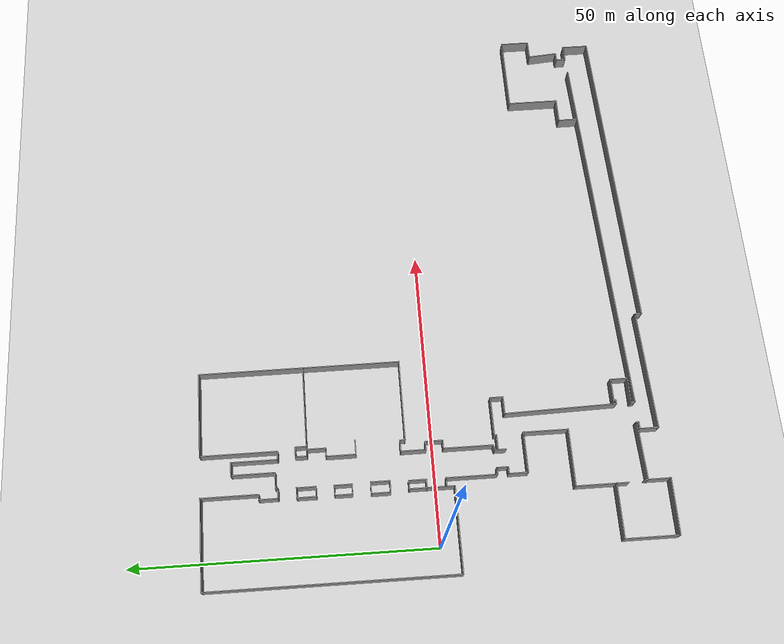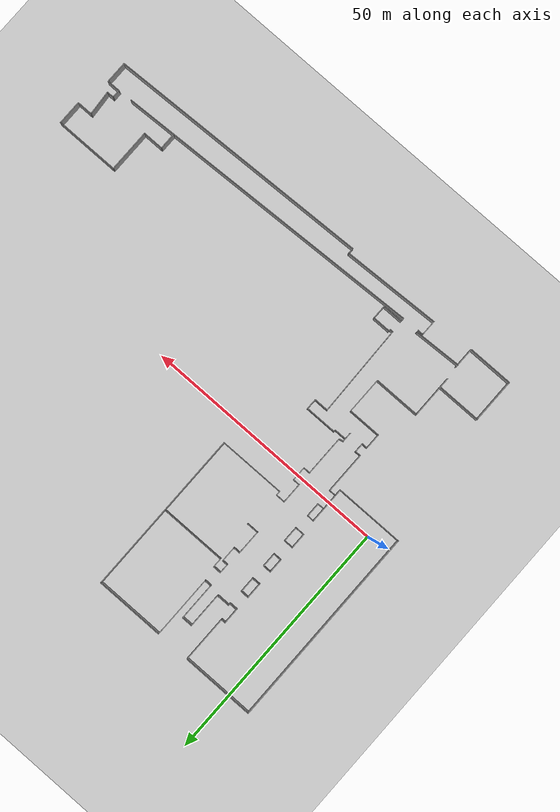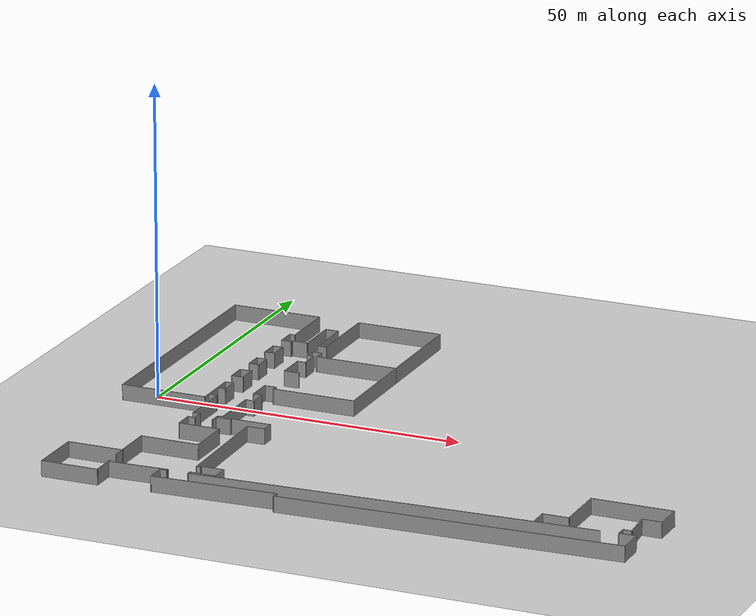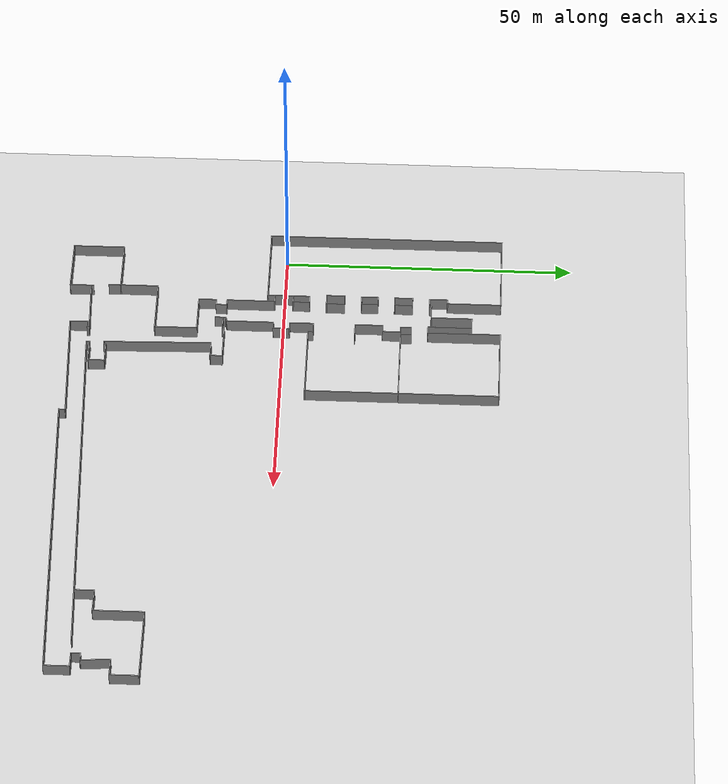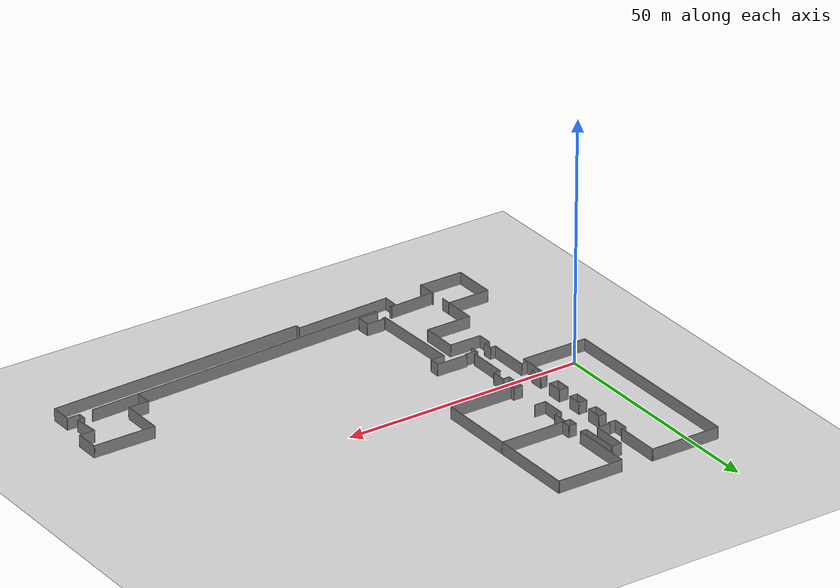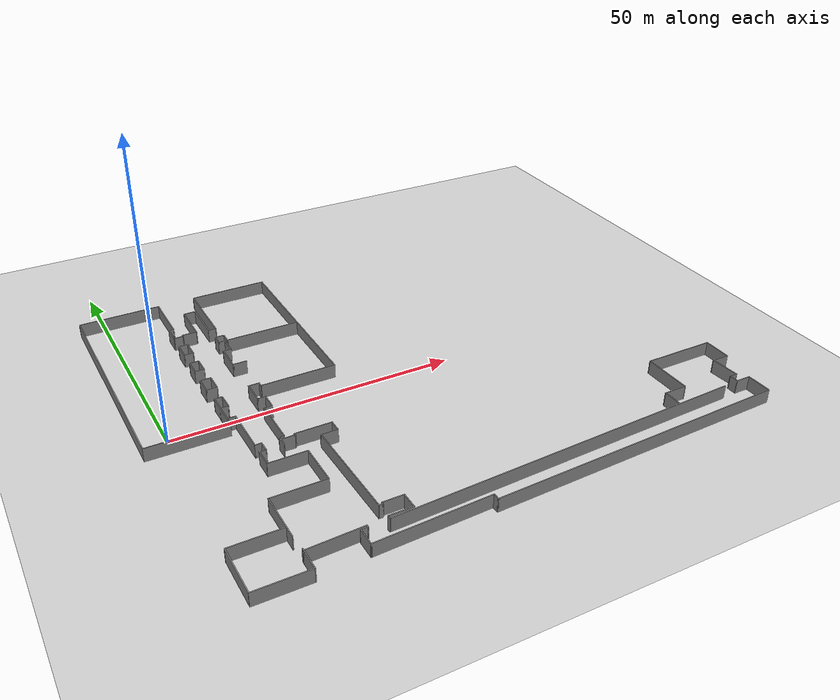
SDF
<sdf version="1.7">
 <world name="default">
  <light name="sun" type="directional">
   <pose>0 0 10 0 -0 0</pose>
   <diffuse>0.8 0.8 0.8 1</diffuse>
   <specular>0.2 0.2 0.2 1</specular>
   <attenuation>
    <range>1000</range>
    <constant>0.9</constant>
    <linear>0.01</linear>
    <quadratic>0.001</quadratic>
   </attenuation>
   <direction>-0.5 0.1 -0.9</direction>
   <spot><inner_angle>0</inner_angle><outer_angle>0</outer_angle><falloff>0</falloff></spot>
  </light>
  <model name="ground_plane">
   <static>1</static>
   <link name="link">
    <collision name="collision">
     <geometry><plane><normal>0 0 1</normal><size>100 100</size></plane></geometry>
     <surface>
      <contact><collide_bitmask>65535</collide_bitmask></contact>
      <friction><ode><mu>100</mu><mu2>50</mu2></ode></friction>
     </surface>
    </collision>
    <visual name="visual">
     <cast_shadows>0</cast_shadows>
     <geometry><plane><normal>0 0 1</normal><size>100 100</size></plane></geometry>
     <material>
      <script><uri>file://media/materials/scripts/gazebo.material</uri><name>Gazebo/Grey</name></script>
     </material>
    </visual>
   </link>
  </model>
  <gravity>0 0 -9.8</gravity>
  <magnetic_field>6e-06 2.3e-05 -4.2e-05</magnetic_field>
  <atmosphere type="adiabatic"/>
  <physics type="ode">
   <max_step_size>0.001</max_step_size>
   <real_time_factor>1</real_time_factor>
   <real_time_update_rate>1000</real_time_update_rate>
  </physics>
  <scene><ambient>0.4 0.4 0.4 1</ambient><background>0.7 0.7 0.7 1</background><shadows>1</shadows></scene>
  <spherical_coordinates>
   <surface_model>EARTH_WGS84</surface_model>
   <latitude_deg>0</latitude_deg>
   <longitude_deg>0</longitude_deg>
   <elevation>0</elevation>
   <heading_deg>0</heading_deg>
  </spherical_coordinates>
  <model name="Lab">
   <pose>43.6591 0.026965 -0.000316 0 -1.4e-05 -1.57</pose>
   <link name="Wall_100">
    <collision name="Wall_100_Collision">
     <geometry><box><size>9.5 0.15 2.5</size></box></geometry>
     <pose>0 0 1.25 0 -0 0</pose>
    </collision>
    <visual name="Wall_100_Visual">
     <pose>0 0 1.25 0 -0 0</pose>
     <geometry><box><size>9.5 0.15 2.5</size></box></geometry>
     <material>
      <script><uri>file://media/materials/scripts/gazebo.material</uri><name>Gazebo/Grey</name></script>
      <ambient>1 1 1 1</ambient>
     </material>
     <meta><layer>0</layer></meta>
    </visual>
    <pose>22.3849 -30.9913 0 0 -0 -1.5708</pose>
    <inertial>
     <inertia><ixx>1</ixx><ixy>0</ixy><ixz>0</ixz><iyy>1</iyy><iyz>0</iyz><izz>1</izz></inertia>
     <mass>1</mass>
    </inertial>
   </link>
   <link name="Wall_101">
    <collision name="Wall_101_Collision">
     <geometry><box><size>8.75 0.15 2.5</size></box></geometry>
     <pose>0 0 1.25 0 -0 0</pose>
    </collision>
    <visual name="Wall_101_Visual">
     <pose>0 0 1.25 0 -0 0</pose>
     <geometry><box><size>8.75 0.15 2.5</size></box></geometry>
     <material>
      <script><uri>file://media/materials/scripts/gazebo.material</uri><name>Gazebo/Grey</name></script>
      <ambient>1 1 1 1</ambient>
     </material>
     <meta><layer>0</layer></meta>
    </visual>
    <pose>26.6849 -35.6663 0 0 -0 0</pose>
    <inertial>
     <inertia><ixx>1</ixx><ixy>0</ixy><ixz>0</ixz><iyy>1</iyy><iyz>0</iyz><izz>1</izz></inertia>
     <mass>1</mass>
    </inertial>
   </link>
   <link name="Wall_103">
    <collision name="Wall_103_Collision">
     <geometry><box><size>9 0.15 2.5</size></box></geometry>
     <pose>0 0 1.25 0 -0 0</pose>
    </collision>
    <visual name="Wall_103_Visual">
     <pose>0 0 1.25 0 -0 0</pose>
     <geometry><box><size>9 0.15 2.5</size></box></geometry>
     <material>
      <script><uri>file://media/materials/scripts/gazebo.material</uri><name>Gazebo/Grey</name></script>
      <ambient>1 1 1 1</ambient>
     </material>
     <meta><layer>0</layer></meta>
    </visual>
    <pose>28.9663 -40.0681 0 0 -0 -1.5708</pose>
    <inertial>
     <inertia><ixx>1</ixx><ixy>0</ixy><ixz>0</ixz><iyy>1</iyy><iyz>0</iyz><izz>1</izz></inertia>
     <mass>1</mass>
    </inertial>
   </link>
   <link name="Wall_104">
    <collision name="Wall_104_Collision">
     <geometry><box><size>9 0.15 2.5</size></box></geometry>
     <pose>0 0 1.25 0 -0 0</pose>
    </collision>
    <visual name="Wall_104_Visual">
     <pose>0 0 1.25 0 -0 0</pose>
     <geometry><box><size>9 0.15 2.5</size></box></geometry>
     <material>
      <script><uri>file://media/materials/scripts/gazebo.material</uri><name>Gazebo/Grey</name></script>
      <ambient>1 1 1 1</ambient>
     </material>
     <meta><layer>0</layer></meta>
    </visual>
    <pose>33.3913 -44.4931 0 0 -0 0</pose>
    <inertial>
     <inertia><ixx>1</ixx><ixy>0</ixy><ixz>0</ixz><iyy>1</iyy><iyz>0</iyz><izz>1</izz></inertia>
     <mass>1</mass>
    </inertial>
   </link>
   <link name="Wall_105">
    <collision name="Wall_105_Collision">
     <geometry><box><size>9.25 0.15 2.5</size></box></geometry>
     <pose>0 0 1.25 0 -0 0</pose>
    </collision>
    <visual name="Wall_105_Visual">
     <pose>0 0 1.25 0 -0 0</pose>
     <geometry><box><size>9.25 0.15 2.5</size></box></geometry>
     <material>
      <script><uri>file://media/materials/scripts/gazebo.material</uri><name>Gazebo/Grey</name></script>
      <ambient>1 1 1 1</ambient>
     </material>
     <meta><layer>0</layer></meta>
    </visual>
    <pose>37.8163 -39.9431 0 0 -0 1.5708</pose>
    <inertial>
     <inertia><ixx>1</ixx><ixy>0</ixy><ixz>0</ixz><iyy>1</iyy><iyz>0</iyz><izz>1</izz></inertia>
     <mass>1</mass>
    </inertial>
   </link>
   <link name="Wall_106">
    <collision name="Wall_106_Collision">
     <geometry><box><size>4.25 0.15 2.5</size></box></geometry>
     <pose>0 0 1.25 0 -0 0</pose>
    </collision>
    <visual name="Wall_106_Visual">
     <pose>0 0 1.25 0 -0 0</pose>
     <geometry><box><size>4.25 0.15 2.5</size></box></geometry>
     <material>
      <script><uri>file://media/materials/scripts/gazebo.material</uri><name>Gazebo/Grey</name></script>
      <ambient>1 1 1 1</ambient>
     </material>
     <meta><layer>0</layer></meta>
    </visual>
    <pose>35.7663 -35.3931 0 0 -0 3.14159</pose>
    <inertial>
     <inertia><ixx>1</ixx><ixy>0</ixy><ixz>0</ixz><iyy>1</iyy><iyz>0</iyz><izz>1</izz></inertia>
     <mass>1</mass>
    </inertial>
   </link>
   <link name="Wall_112">
    <collision name="Wall_112_Collision">
     <geometry><box><size>9.66481 0.15 2.5</size></box></geometry>
     <pose>0 0 1.25 0 -0 0</pose>
    </collision>
    <visual name="Wall_112_Visual">
     <pose>0 0 1.25 0 -0 0</pose>
     <geometry><box><size>9.66481 0.15 2.5</size></box></geometry>
     <material>
      <script><uri>file://media/materials/scripts/gazebo.material</uri><name>Gazebo/Grey</name></script>
      <ambient>1 1 1 1</ambient>
     </material>
     <meta><layer>0</layer></meta>
    </visual>
    <pose>33.9278 -30.6585 0 0 -0 1.61214</pose>
    <inertial>
     <inertia><ixx>1</ixx><ixy>0</ixy><ixz>0</ixz><iyy>1</iyy><iyz>0</iyz><izz>1</izz></inertia>
     <mass>1</mass>
    </inertial>
   </link>
   <link name="Wall_113">
    <collision name="Wall_113_Collision">
     <geometry><box><size>0.5 0.15 2.5</size></box></geometry>
     <pose>0 0 1.25 0 -0 0</pose>
    </collision>
    <visual name="Wall_113_Visual">
     <pose>0 0 1.25 0 -0 0</pose>
     <geometry><box><size>0.5 0.15 2.5</size></box></geometry>
     <material>
      <script><uri>file://media/materials/scripts/gazebo.material</uri><name>Gazebo/Grey</name></script>
      <ambient>1 1 1 1</ambient>
     </material>
     <meta><layer>0</layer></meta>
    </visual>
    <pose>33.9062 -25.9051 0 0 -0 0</pose>
    <inertial>
     <inertia><ixx>1</ixx><ixy>0</ixy><ixz>0</ixz><iyy>1</iyy><iyz>0</iyz><izz>1</izz></inertia>
     <mass>1</mass>
    </inertial>
   </link>
   <link name="Wall_114">
    <collision name="Wall_114_Collision">
     <geometry><box><size>1.25 0.15 2.5</size></box></geometry>
     <pose>0 0 1.25 0 -0 0</pose>
    </collision>
    <visual name="Wall_114_Visual">
     <pose>0 0 1.25 0 -0 0</pose>
     <geometry><box><size>1.25 0.15 2.5</size></box></geometry>
     <material>
      <script><uri>file://media/materials/scripts/gazebo.material</uri><name>Gazebo/Grey</name></script>
      <ambient>1 1 1 1</ambient>
     </material>
     <meta><layer>0</layer></meta>
    </visual>
    <pose>34.0812 -26.4551 0 0 -0 -1.5708</pose>
    <inertial>
     <inertia><ixx>1</ixx><ixy>0</ixy><ixz>0</ixz><iyy>1</iyy><iyz>0</iyz><izz>1</izz></inertia>
     <mass>1</mass>
    </inertial>
   </link>
   <link name="Wall_115">
    <collision name="Wall_115_Collision">
     <geometry><box><size>3.25 0.15 2.5</size></box></geometry>
     <pose>0 0 1.25 0 -0 0</pose>
    </collision>
    <visual name="Wall_115_Visual">
     <pose>0 0 1.25 0 -0 0</pose>
     <geometry><box><size>3.25 0.15 2.5</size></box></geometry>
     <material>
      <script><uri>file://media/materials/scripts/gazebo.material</uri><name>Gazebo/Grey</name></script>
      <ambient>1 1 1 1</ambient>
     </material>
     <meta><layer>0</layer></meta>
    </visual>
    <pose>35.6312 -27.0051 0 0 -0 0</pose>
    <inertial>
     <inertia><ixx>1</ixx><ixy>0</ixy><ixz>0</ixz><iyy>1</iyy><iyz>0</iyz><izz>1</izz></inertia>
     <mass>1</mass>
    </inertial>
   </link>
   <link name="Wall_117">
    <collision name="Wall_117_Collision">
     <geometry><box><size>3 0.15 2.5</size></box></geometry>
     <pose>0 0 1.25 0 -0 0</pose>
    </collision>
    <visual name="Wall_117_Visual">
     <pose>0 0 1.25 0 -0 0</pose>
     <geometry><box><size>3 0.15 2.5</size></box></geometry>
     <material>
      <script><uri>file://media/materials/scripts/gazebo.material</uri><name>Gazebo/Grey</name></script>
      <ambient>1 1 1 1</ambient>
     </material>
     <meta><layer>0</layer></meta>
    </visual>
    <pose>31.9611 -18.3743 0 0 -0 0</pose>
    <inertial>
     <inertia><ixx>1</ixx><ixy>0</ixy><ixz>0</ixz><iyy>1</iyy><iyz>0</iyz><izz>1</izz></inertia>
     <mass>1</mass>
    </inertial>
   </link>
   <link name="Wall_118">
    <collision name="Wall_118_Collision">
     <geometry><box><size>4.25 0.15 2.5</size></box></geometry>
     <pose>0 0 1.25 0 -0 0</pose>
    </collision>
    <visual name="Wall_118_Visual">
     <pose>0 0 1.25 0 -0 0</pose>
     <geometry><box><size>4.25 0.15 2.5</size></box></geometry>
     <material>
      <script><uri>file://media/materials/scripts/gazebo.material</uri><name>Gazebo/Grey</name></script>
      <ambient>1 1 1 1</ambient>
     </material>
     <meta><layer>0</layer></meta>
    </visual>
    <pose>33.3861 -20.4243 0 0 -0 -1.5708</pose>
    <inertial>
     <inertia><ixx>1</ixx><ixy>0</ixy><ixz>0</ixz><iyy>1</iyy><iyz>0</iyz><izz>1</izz></inertia>
     <mass>1</mass>
    </inertial>
   </link>
   <link name="Wall_119">
    <collision name="Wall_119_Collision">
     <geometry><box><size>0.75 0.15 2.5</size></box></geometry>
     <pose>0 0 1.25 0 -0 0</pose>
    </collision>
    <visual name="Wall_119_Visual">
     <pose>0 0 1.25 0 -0 0</pose>
     <geometry><box><size>0.75 0.15 2.5</size></box></geometry>
     <material>
      <script><uri>file://media/materials/scripts/gazebo.material</uri><name>Gazebo/Grey</name></script>
      <ambient>1 1 1 1</ambient>
     </material>
     <meta><layer>0</layer></meta>
    </visual>
    <pose>33.6861 -22.4743 0 0 -0 0</pose>
    <inertial>
     <inertia><ixx>1</ixx><ixy>0</ixy><ixz>0</ixz><iyy>1</iyy><iyz>0</iyz><izz>1</izz></inertia>
     <mass>1</mass>
    </inertial>
   </link>
   <link name="Wall_12">
    <collision name="Wall_12_Collision">
     <geometry><box><size>14.75 0.15 2.5</size></box></geometry>
     <pose>0 0 1.25 0 -0 0</pose>
    </collision>
    <visual name="Wall_12_Visual">
     <pose>0 0 1.25 0 -0 0</pose>
     <geometry><box><size>14.75 0.15 2.5</size></box></geometry>
     <material>
      <script><uri>file://media/materials/scripts/gazebo.material</uri><name>Gazebo/Grey</name></script>
      <ambient>1 1 1 1</ambient>
     </material>
     <meta><layer>0</layer></meta>
    </visual>
    <pose>-37.8163 -40.8414 0 0 -0 1.5708</pose>
    <inertial>
     <inertia><ixx>1</ixx><ixy>0</ixy><ixz>0</ixz><iyy>1</iyy><iyz>0</iyz><izz>1</izz></inertia>
     <mass>1</mass>
    </inertial>
   </link>
   <link name="Wall_121">
    <collision name="Wall_121_Collision">
     <geometry><box><size>20.026 0.15 2.5</size></box></geometry>
     <pose>0 0 1.25 0 -0 0</pose>
    </collision>
    <visual name="Wall_121_Visual">
     <pose>0 0 1.25 0 -0 0</pose>
     <geometry><box><size>20.026 0.15 2.5</size></box></geometry>
     <material>
      <script><uri>file://media/materials/scripts/gazebo.material</uri><name>Gazebo/Grey</name></script>
      <ambient>1 1 1 1</ambient>
     </material>
     <meta><layer>0</layer></meta>
    </visual>
    <pose>36.7959 -17.0746 0 0 -0 1.60957</pose>
    <inertial>
     <inertia><ixx>1</ixx><ixy>0</ixy><ixz>0</ixz><iyy>1</iyy><iyz>0</iyz><izz>1</izz></inertia>
     <mass>1</mass>
    </inertial>
   </link>
   <link name="Wall_123">
    <collision name="Wall_123_Collision">
     <geometry><box><size>1.25 0.15 2.5</size></box></geometry>
     <pose>0 0 1.25 0 -0 0</pose>
    </collision>
    <visual name="Wall_123_Visual">
     <pose>0 0 1.25 0 -0 0</pose>
     <geometry><box><size>1.25 0.15 2.5</size></box></geometry>
     <material>
      <script><uri>file://media/materials/scripts/gazebo.material</uri><name>Gazebo/Grey</name></script>
      <ambient>1 1 1 1</ambient>
     </material>
     <meta><layer>0</layer></meta>
    </visual>
    <pose>36.9607 -7.14408 0 0 -0 0</pose>
    <inertial>
     <inertia><ixx>1</ixx><ixy>0</ixy><ixz>0</ixz><iyy>1</iyy><iyz>0</iyz><izz>1</izz></inertia>
     <mass>1</mass>
    </inertial>
   </link>
   <link name="Wall_125">
    <collision name="Wall_125_Collision">
     <geometry><box><size>63.8964 0.15 2.5</size></box></geometry>
     <pose>0 0 1.25 0 -0 0</pose>
    </collision>
    <visual name="Wall_125_Visual">
     <pose>0 0 1.25 0 -0 0</pose>
     <geometry><box><size>63.8964 0.15 2.5</size></box></geometry>
     <material>
      <script><uri>file://media/materials/scripts/gazebo.material</uri><name>Gazebo/Grey</name></script>
      <ambient>1 1 1 1</ambient>
     </material>
     <meta><layer>0</layer></meta>
    </visual>
    <pose>32.6938 9.3727 0 0 -0 1.61135</pose>
    <inertial>
     <inertia><ixx>1</ixx><ixy>0</ixy><ixz>0</ixz><iyy>1</iyy><iyz>0</iyz><izz>1</izz></inertia>
     <mass>1</mass>
    </inertial>
   </link>
   <link name="Wall_127">
    <collision name="Wall_127_Collision">
     <geometry><box><size>3.5 0.15 2.5</size></box></geometry>
     <pose>0 0 1.25 0 -0 0</pose>
    </collision>
    <visual name="Wall_127_Visual">
     <pose>0 0 1.25 0 -0 0</pose>
     <geometry><box><size>3.5 0.15 2.5</size></box></geometry>
     <material>
      <script><uri>file://media/materials/scripts/gazebo.material</uri><name>Gazebo/Grey</name></script>
      <ambient>1 1 1 1</ambient>
     </material>
     <meta><layer>0</layer></meta>
    </visual>
    <pose>30.0989 31.1914 0 0 -0 3.14159</pose>
    <inertial>
     <inertia><ixx>1</ixx><ixy>0</ixy><ixz>0</ixz><iyy>1</iyy><iyz>0</iyz><izz>1</izz></inertia>
     <mass>1</mass>
    </inertial>
   </link>
   <link name="Wall_128">
    <collision name="Wall_128_Collision">
     <geometry><box><size>4.25 0.15 2.5</size></box></geometry>
     <pose>0 0 1.25 0 -0 0</pose>
    </collision>
    <visual name="Wall_128_Visual">
     <pose>0 0 1.25 0 -0 0</pose>
     <geometry><box><size>4.25 0.15 2.5</size></box></geometry>
     <material>
      <script><uri>file://media/materials/scripts/gazebo.material</uri><name>Gazebo/Grey</name></script>
      <ambient>1 1 1 1</ambient>
     </material>
     <meta><layer>0</layer></meta>
    </visual>
    <pose>28.4239 33.2414 0 0 -0 1.5708</pose>
    <inertial>
     <inertia><ixx>1</ixx><ixy>0</ixy><ixz>0</ixz><iyy>1</iyy><iyz>0</iyz><izz>1</izz></inertia>
     <mass>1</mass>
    </inertial>
   </link>
   <link name="Wall_129">
    <collision name="Wall_129_Collision">
     <geometry><box><size>8.75 0.15 2.5</size></box></geometry>
     <pose>0 0 1.25 0 -0 0</pose>
    </collision>
    <visual name="Wall_129_Visual">
     <pose>0 0 1.25 0 -0 0</pose>
     <geometry><box><size>8.75 0.15 2.5</size></box></geometry>
     <material>
      <script><uri>file://media/materials/scripts/gazebo.material</uri><name>Gazebo/Grey</name></script>
      <ambient>1 1 1 1</ambient>
     </material>
     <meta><layer>0</layer></meta>
    </visual>
    <pose>24.1239 35.2914 0 0 -0 3.14159</pose>
    <inertial>
     <inertia><ixx>1</ixx><ixy>0</ixy><ixz>0</ixz><iyy>1</iyy><iyz>0</iyz><izz>1</izz></inertia>
     <mass>1</mass>
    </inertial>
   </link>
   <link name="Wall_131">
    <collision name="Wall_131_Collision">
     <geometry><box><size>13 0.15 2.5</size></box></geometry>
     <pose>0 0 1.25 0 -0 0</pose>
    </collision>
    <visual name="Wall_131_Visual">
     <pose>0 0 1.25 0 -0 0</pose>
     <geometry><box><size>13 0.15 2.5</size></box></geometry>
     <material>
      <script><uri>file://media/materials/scripts/gazebo.material</uri><name>Gazebo/Grey</name></script>
      <ambient>1 1 1 1</ambient>
     </material>
     <meta><layer>0</layer></meta>
    </visual>
    <pose>19.8239 41.7164 0 0 -0 1.5708</pose>
    <inertial>
     <inertia><ixx>1</ixx><ixy>0</ixy><ixz>0</ixz><iyy>1</iyy><iyz>0</iyz><izz>1</izz></inertia>
     <mass>1</mass>
    </inertial>
   </link>
   <link name="Wall_132">
    <collision name="Wall_132_Collision">
     <geometry><box><size>5 0.15 2.5</size></box></geometry>
     <pose>0 0 1.25 0 -0 0</pose>
    </collision>
    <visual name="Wall_132_Visual">
     <pose>0 0 1.25 0 -0 0</pose>
     <geometry><box><size>5 0.15 2.5</size></box></geometry>
     <material>
      <script><uri>file://media/materials/scripts/gazebo.material</uri><name>Gazebo/Grey</name></script>
      <ambient>1 1 1 1</ambient>
     </material>
     <meta><layer>0</layer></meta>
    </visual>
    <pose>22.2489 48.1414 0 0 -0 0</pose>
    <inertial>
     <inertia><ixx>1</ixx><ixy>0</ixy><ixz>0</ixz><iyy>1</iyy><iyz>0</iyz><izz>1</izz></inertia>
     <mass>1</mass>
    </inertial>
   </link>
   <link name="Wall_133">
    <collision name="Wall_133_Collision">
     <geometry><box><size>3.25 0.15 2.5</size></box></geometry>
     <pose>0 0 1.25 0 -0 0</pose>
    </collision>
    <visual name="Wall_133_Visual">
     <pose>0 0 1.25 0 -0 0</pose>
     <geometry><box><size>3.25 0.15 2.5</size></box></geometry>
     <material>
      <script><uri>file://media/materials/scripts/gazebo.material</uri><name>Gazebo/Grey</name></script>
      <ambient>1 1 1 1</ambient>
     </material>
     <meta><layer>0</layer></meta>
    </visual>
    <pose>24.6739 46.5914 0 0 -0 -1.5708</pose>
    <inertial>
     <inertia><ixx>1</ixx><ixy>0</ixy><ixz>0</ixz><iyy>1</iyy><iyz>0</iyz><izz>1</izz></inertia>
     <mass>1</mass>
    </inertial>
   </link>
   <link name="Wall_134">
    <collision name="Wall_134_Collision">
     <geometry><box><size>5.13657 0.15 2.5</size></box></geometry>
     <pose>0 0 1.25 0 -0 0</pose>
    </collision>
    <visual name="Wall_134_Visual">
     <pose>0 0 1.25 0 -0 0</pose>
     <geometry><box><size>5.13657 0.15 2.5</size></box></geometry>
     <material>
      <script><uri>file://media/materials/scripts/gazebo.material</uri><name>Gazebo/Grey</name></script>
      <ambient>1 1 1 1</ambient>
     </material>
     <meta><layer>0</layer></meta>
    </visual>
    <pose>27.1599 45.232 0 0 -0 0.076501</pose>
    <inertial>
     <inertia><ixx>1</ixx><ixy>0</ixy><ixz>0</ixz><iyy>1</iyy><iyz>0</iyz><izz>1</izz></inertia>
     <mass>1</mass>
    </inertial>
   </link>
   <link name="Wall_135">
    <collision name="Wall_135_Collision">
     <geometry><box><size>1.5 0.15 2.5</size></box></geometry>
     <pose>0 0 1.25 0 -0 0</pose>
    </collision>
    <visual name="Wall_135_Visual">
     <pose>0 0 1.25 0 -0 0</pose>
     <geometry><box><size>1.5 0.15 2.5</size></box></geometry>
     <material>
      <script><uri>file://media/materials/scripts/gazebo.material</uri><name>Gazebo/Grey</name></script>
      <ambient>1 1 1 1</ambient>
     </material>
     <meta><layer>0</layer></meta>
    </visual>
    <pose>29.6458 44.7475 0 0 -0 -1.5708</pose>
    <inertial>
     <inertia><ixx>1</ixx><ixy>0</ixy><ixz>0</ixz><iyy>1</iyy><iyz>0</iyz><izz>1</izz></inertia>
     <mass>1</mass>
    </inertial>
   </link>
   <link name="Wall_136">
    <collision name="Wall_136_Collision">
     <geometry><box><size>1.75 0.15 2.5</size></box></geometry>
     <pose>0 0 1.25 0 -0 0</pose>
    </collision>
    <visual name="Wall_136_Visual">
     <pose>0 0 1.25 0 -0 0</pose>
     <geometry><box><size>1.75 0.15 2.5</size></box></geometry>
     <material>
      <script><uri>file://media/materials/scripts/gazebo.material</uri><name>Gazebo/Grey</name></script>
      <ambient>1 1 1 1</ambient>
     </material>
     <meta><layer>0</layer></meta>
    </visual>
    <pose>30.4458 44.0725 0 0 -0 0</pose>
    <inertial>
     <inertia><ixx>1</ixx><ixy>0</ixy><ixz>0</ixz><iyy>1</iyy><iyz>0</iyz><izz>1</izz></inertia>
     <mass>1</mass>
    </inertial>
   </link>
   <link name="Wall_137">
    <collision name="Wall_137_Collision">
     <geometry><box><size>2.75 0.15 2.5</size></box></geometry>
     <pose>0 0 1.25 0 -0 0</pose>
    </collision>
    <visual name="Wall_137_Visual">
     <pose>0 0 1.25 0 -0 0</pose>
     <geometry><box><size>2.75 0.15 2.5</size></box></geometry>
     <material>
      <script><uri>file://media/materials/scripts/gazebo.material</uri><name>Gazebo/Grey</name></script>
      <ambient>1 1 1 1</ambient>
     </material>
     <meta><layer>0</layer></meta>
    </visual>
    <pose>31.2458 45.3725 0 0 -0 1.5708</pose>
    <inertial>
     <inertia><ixx>1</ixx><ixy>0</ixy><ixz>0</ixz><iyy>1</iyy><iyz>0</iyz><izz>1</izz></inertia>
     <mass>1</mass>
    </inertial>
   </link>
   <link name="Wall_138">
    <collision name="Wall_138_Collision">
     <geometry><box><size>4.5 0.15 2.5</size></box></geometry>
     <pose>0 0 1.25 0 -0 0</pose>
    </collision>
    <visual name="Wall_138_Visual">
     <pose>0 0 1.25 0 -0 0</pose>
     <geometry><box><size>4.5 0.15 2.5</size></box></geometry>
     <material>
      <script><uri>file://media/materials/scripts/gazebo.material</uri><name>Gazebo/Grey</name></script>
      <ambient>1 1 1 1</ambient>
     </material>
     <meta><layer>0</layer></meta>
    </visual>
    <pose>33.4208 46.6725 0 0 -0 0</pose>
    <inertial>
     <inertia><ixx>1</ixx><ixy>0</ixy><ixz>0</ixz><iyy>1</iyy><iyz>0</iyz><izz>1</izz></inertia>
     <mass>1</mass>
    </inertial>
   </link>
   <link name="Wall_14">
    <collision name="Wall_14_Collision">
     <geometry><box><size>9.5 0.15 2.5</size></box></geometry>
     <pose>0 0 1.25 0 -0 0</pose>
    </collision>
    <visual name="Wall_14_Visual">
     <pose>0 0 1.25 0 -0 0</pose>
     <geometry><box><size>9.5 0.15 2.5</size></box></geometry>
     <material>
      <script><uri>file://media/materials/scripts/gazebo.material</uri><name>Gazebo/Grey</name></script>
      <ambient>1 1 1 1</ambient>
     </material>
     <meta><layer>0</layer></meta>
    </visual>
    <pose>-33.1413 -33.5414 0 0 -0 0</pose>
    <inertial>
     <inertia><ixx>1</ixx><ixy>0</ixy><ixz>0</ixz><iyy>1</iyy><iyz>0</iyz><izz>1</izz></inertia>
     <mass>1</mass>
    </inertial>
   </link>
   <link name="Wall_140">
    <collision name="Wall_140_Collision">
     <geometry><box><size>53.9783 0.15 2.5</size></box></geometry>
     <pose>0 0 1.25 0 -0 0</pose>
    </collision>
    <visual name="Wall_140_Visual">
     <pose>0 0 1.25 0 -0 0</pose>
     <geometry><box><size>53.9783 0.15 2.5</size></box></geometry>
     <material>
      <script><uri>file://media/materials/scripts/gazebo.material</uri><name>Gazebo/Grey</name></script>
      <ambient>1 1 1 1</ambient>
     </material>
     <meta><layer>0</layer></meta>
    </visual>
    <pose>36.5596 19.7533 0 0 -0 1.60614</pose>
    <inertial>
     <inertia><ixx>1</ixx><ixy>0</ixy><ixz>0</ixz><iyy>1</iyy><iyz>0</iyz><izz>1</izz></inertia>
     <mass>1</mass>
    </inertial>
   </link>
   <link name="Wall_15">
    <collision name="Wall_15_Collision">
     <geometry><box><size>1 0.15 2.5</size></box></geometry>
     <pose>0 0 1.25 0 -0 0</pose>
    </collision>
    <visual name="Wall_15_Visual">
     <pose>0 0 1.25 0 -0 0</pose>
     <geometry><box><size>1 0.15 2.5</size></box></geometry>
     <material>
      <script><uri>file://media/materials/scripts/gazebo.material</uri><name>Gazebo/Grey</name></script>
      <ambient>1 1 1 1</ambient>
     </material>
     <meta><layer>0</layer></meta>
    </visual>
    <pose>-28.4663 -33.9664 0 0 -0 -1.5708</pose>
    <inertial>
     <inertia><ixx>1</ixx><ixy>0</ixy><ixz>0</ixz><iyy>1</iyy><iyz>0</iyz><izz>1</izz></inertia>
     <mass>1</mass>
    </inertial>
   </link>
   <link name="Wall_16">
    <collision name="Wall_16_Collision">
     <geometry><box><size>3.25 0.15 2.5</size></box></geometry>
     <pose>0 0 1.25 0 -0 0</pose>
    </collision>
    <visual name="Wall_16_Visual">
     <pose>0 0 1.25 0 -0 0</pose>
     <geometry><box><size>3.25 0.15 2.5</size></box></geometry>
     <material>
      <script><uri>file://media/materials/scripts/gazebo.material</uri><name>Gazebo/Grey</name></script>
      <ambient>1 1 1 1</ambient>
     </material>
     <meta><layer>0</layer></meta>
    </visual>
    <pose>-26.9163 -34.3914 0 0 -0 0</pose>
    <inertial>
     <inertia><ixx>1</ixx><ixy>0</ixy><ixz>0</ixz><iyy>1</iyy><iyz>0</iyz><izz>1</izz></inertia>
     <mass>1</mass>
    </inertial>
   </link>
   <link name="Wall_17">
    <collision name="Wall_17_Collision">
     <geometry><box><size>1.75 0.15 2.5</size></box></geometry>
     <pose>0 0 1.25 0 -0 0</pose>
    </collision>
    <visual name="Wall_17_Visual">
     <pose>0 0 1.25 0 -0 0</pose>
     <geometry><box><size>1.75 0.15 2.5</size></box></geometry>
     <material>
      <script><uri>file://media/materials/scripts/gazebo.material</uri><name>Gazebo/Grey</name></script>
      <ambient>1 1 1 1</ambient>
     </material>
     <meta><layer>0</layer></meta>
    </visual>
    <pose>-25.3663 -33.5914 0 0 -0 1.5708</pose>
    <inertial>
     <inertia><ixx>1</ixx><ixy>0</ixy><ixz>0</ixz><iyy>1</iyy><iyz>0</iyz><izz>1</izz></inertia>
     <mass>1</mass>
    </inertial>
   </link>
   <link name="Wall_20">
    <collision name="Wall_20_Collision">
     <geometry><box><size>0.5 0.15 2.5</size></box></geometry>
     <pose>0 0 1.25 0 -0 0</pose>
    </collision>
    <visual name="Wall_20_Visual">
     <pose>0 0 1.25 0 -0 0</pose>
     <geometry><box><size>0.5 0.15 2.5</size></box></geometry>
     <material>
      <script><uri>file://media/materials/scripts/gazebo.material</uri><name>Gazebo/Grey</name></script>
      <ambient>1 1 1 1</ambient>
     </material>
     <meta><layer>0</layer></meta>
    </visual>
    <pose>-25.5413 -32.7914 0 0 -0 3.14159</pose>
    <inertial>
     <inertia><ixx>1</ixx><ixy>0</ixy><ixz>0</ixz><iyy>1</iyy><iyz>0</iyz><izz>1</izz></inertia>
     <mass>1</mass>
    </inertial>
   </link>
   <link name="Wall_21">
    <collision name="Wall_21_Collision">
     <geometry><box><size>2.75 0.15 2.5</size></box></geometry>
     <pose>0 0 1.25 0 -0 0</pose>
    </collision>
    <visual name="Wall_21_Visual">
     <pose>0 0 1.25 0 -0 0</pose>
     <geometry><box><size>2.75 0.15 2.5</size></box></geometry>
     <material>
      <script><uri>file://media/materials/scripts/gazebo.material</uri><name>Gazebo/Grey</name></script>
      <ambient>1 1 1 1</ambient>
     </material>
     <meta><layer>0</layer></meta>
    </visual>
    <pose>-25.7163 -31.4914 0 0 -0 1.5708</pose>
    <inertial>
     <inertia><ixx>1</ixx><ixy>0</ixy><ixz>0</ixz><iyy>1</iyy><iyz>0</iyz><izz>1</izz></inertia>
     <mass>1</mass>
    </inertial>
   </link>
   <link name="Wall_23">
    <collision name="Wall_23_Collision">
     <geometry><box><size>7.25 0.15 2.5</size></box></geometry>
     <pose>0 0 1.25 0 -0 0</pose>
    </collision>
    <visual name="Wall_23_Visual">
     <pose>0 0 1.25 0 -0 0</pose>
     <geometry><box><size>7.25 0.15 2.5</size></box></geometry>
     <material>
      <script><uri>file://media/materials/scripts/gazebo.material</uri><name>Gazebo/Grey</name></script>
      <ambient>1 1 1 1</ambient>
     </material>
     <meta><layer>0</layer></meta>
    </visual>
    <pose>-29.2663 -30.1914 0 0 -0 3.14159</pose>
    <inertial>
     <inertia><ixx>1</ixx><ixy>0</ixy><ixz>0</ixz><iyy>1</iyy><iyz>0</iyz><izz>1</izz></inertia>
     <mass>1</mass>
    </inertial>
   </link>
   <link name="Wall_24">
    <collision name="Wall_24_Collision">
     <geometry><box><size>2.25 0.15 2.5</size></box></geometry>
     <pose>0 0 1.25 0 -0 0</pose>
    </collision>
    <visual name="Wall_24_Visual">
     <pose>0 0 1.25 0 -0 0</pose>
     <geometry><box><size>2.25 0.15 2.5</size></box></geometry>
     <material>
      <script><uri>file://media/materials/scripts/gazebo.material</uri><name>Gazebo/Grey</name></script>
      <ambient>1 1 1 1</ambient>
     </material>
     <meta><layer>0</layer></meta>
    </visual>
    <pose>-32.8163 -29.1414 0 0 -0 1.5708</pose>
    <inertial>
     <inertia><ixx>1</ixx><ixy>0</ixy><ixz>0</ixz><iyy>1</iyy><iyz>0</iyz><izz>1</izz></inertia>
     <mass>1</mass>
    </inertial>
   </link>
   <link name="Wall_25">
    <collision name="Wall_25_Collision">
     <geometry><box><size>7.75 0.15 2.5</size></box></geometry>
     <pose>0 0 1.25 0 -0 0</pose>
    </collision>
    <visual name="Wall_25_Visual">
     <pose>0 0 1.25 0 -0 0</pose>
     <geometry><box><size>7.75 0.15 2.5</size></box></geometry>
     <material>
      <script><uri>file://media/materials/scripts/gazebo.material</uri><name>Gazebo/Grey</name></script>
      <ambient>1 1 1 1</ambient>
     </material>
     <meta><layer>0</layer></meta>
    </visual>
    <pose>-29.0163 -28.0914 0 0 -0 0</pose>
    <inertial>
     <inertia><ixx>1</ixx><ixy>0</ixy><ixz>0</ixz><iyy>1</iyy><iyz>0</iyz><izz>1</izz></inertia>
     <mass>1</mass>
    </inertial>
   </link>
   <link name="Wall_26">
    <collision name="Wall_26_Collision">
     <geometry><box><size>1.5 0.15 2.5</size></box></geometry>
     <pose>0 0 1.25 0 -0 0</pose>
    </collision>
    <visual name="Wall_26_Visual">
     <pose>0 0 1.25 0 -0 0</pose>
     <geometry><box><size>1.5 0.15 2.5</size></box></geometry>
     <material>
      <script><uri>file://media/materials/scripts/gazebo.material</uri><name>Gazebo/Grey</name></script>
      <ambient>1 1 1 1</ambient>
     </material>
     <meta><layer>0</layer></meta>
    </visual>
    <pose>-25.2163 -27.4164 0 0 -0 1.5708</pose>
    <inertial>
     <inertia><ixx>1</ixx><ixy>0</ixy><ixz>0</ixz><iyy>1</iyy><iyz>0</iyz><izz>1</izz></inertia>
     <mass>1</mass>
    </inertial>
   </link>
   <link name="Wall_28">
    <collision name="Wall_28_Collision">
     <geometry><box><size>12.75 0.15 2.5</size></box></geometry>
     <pose>0 0 1.25 0 -0 0</pose>
    </collision>
    <visual name="Wall_28_Visual">
     <pose>0 0 1.25 0 -0 0</pose>
     <geometry><box><size>12.75 0.15 2.5</size></box></geometry>
     <material>
      <script><uri>file://media/materials/scripts/gazebo.material</uri><name>Gazebo/Grey</name></script>
      <ambient>1 1 1 1</ambient>
     </material>
     <meta><layer>0</layer></meta>
    </visual>
    <pose>-31.5163 -26.7414 0 0 -0 3.14159</pose>
    <inertial>
     <inertia><ixx>1</ixx><ixy>0</ixy><ixz>0</ixz><iyy>1</iyy><iyz>0</iyz><izz>1</izz></inertia>
     <mass>1</mass>
    </inertial>
   </link>
   <link name="Wall_30">
    <collision name="Wall_30_Collision">
     <geometry><box><size>14 0.15 2.5</size></box></geometry>
     <pose>0 0 1.25 0 -0 0</pose>
    </collision>
    <visual name="Wall_30_Visual">
     <pose>0 0 1.25 0 -0 0</pose>
     <geometry><box><size>14 0.15 2.5</size></box></geometry>
     <material>
      <script><uri>file://media/materials/scripts/gazebo.material</uri><name>Gazebo/Grey</name></script>
      <ambient>1 1 1 1</ambient>
     </material>
     <meta><layer>0</layer></meta>
    </visual>
    <pose>-37.8163 -19.8164 0 0 -0 1.5708</pose>
    <inertial>
     <inertia><ixx>1</ixx><ixy>0</ixy><ixz>0</ixz><iyy>1</iyy><iyz>0</iyz><izz>1</izz></inertia>
     <mass>1</mass>
    </inertial>
   </link>
   <link name="Wall_31">
    <collision name="Wall_31_Collision">
     <geometry><box><size>17.5 0.15 2.5</size></box></geometry>
     <pose>0 0 1.25 0 -0 0</pose>
    </collision>
    <visual name="Wall_31_Visual">
     <pose>0 0 1.25 0 -0 0</pose>
     <geometry><box><size>17.5 0.15 2.5</size></box></geometry>
     <material>
      <script><uri>file://media/materials/scripts/gazebo.material</uri><name>Gazebo/Grey</name></script>
      <ambient>1 1 1 1</ambient>
     </material>
     <meta><layer>0</layer></meta>
    </visual>
    <pose>-29.1413 -12.8914 0 0 -0 0</pose>
    <inertial>
     <inertia><ixx>1</ixx><ixy>0</ixy><ixz>0</ixz><iyy>1</iyy><iyz>0</iyz><izz>1</izz></inertia>
     <mass>1</mass>
    </inertial>
   </link>
   <link name="Wall_32">
    <collision name="Wall_32_Collision">
     <geometry><box><size>13.5 0.15 2.5</size></box></geometry>
     <pose>0 0 1.25 0 -0 0</pose>
    </collision>
    <visual name="Wall_32_Visual">
     <pose>0 0 1.25 0 -0 0</pose>
     <geometry><box><size>13.5 0.15 2.5</size></box></geometry>
     <material>
      <script><uri>file://media/materials/scripts/gazebo.material</uri><name>Gazebo/Grey</name></script>
      <ambient>1 1 1 1</ambient>
     </material>
     <meta><layer>0</layer></meta>
    </visual>
    <pose>-20.4663 -19.5664 0 0 -0 -1.5708</pose>
    <inertial>
     <inertia><ixx>1</ixx><ixy>0</ixy><ixz>0</ixz><iyy>1</iyy><iyz>0</iyz><izz>1</izz></inertia>
     <mass>1</mass>
    </inertial>
   </link>
   <link name="Wall_33">
    <collision name="Wall_33_Collision">
     <geometry><box><size>2 0.15 2.5</size></box></geometry>
     <pose>0 0 1.25 0 -0 0</pose>
    </collision>
    <visual name="Wall_33_Visual">
     <pose>0 0 1.25 0 -0 0</pose>
     <geometry><box><size>2 0.15 2.5</size></box></geometry>
     <material>
      <script><uri>file://media/materials/scripts/gazebo.material</uri><name>Gazebo/Grey</name></script>
      <ambient>1 1 1 1</ambient>
     </material>
     <meta><layer>0</layer></meta>
    </visual>
    <pose>-21.3913 -26.2414 0 0 -0 3.14159</pose>
    <inertial>
     <inertia><ixx>1</ixx><ixy>0</ixy><ixz>0</ixz><iyy>1</iyy><iyz>0</iyz><izz>1</izz></inertia>
     <mass>1</mass>
    </inertial>
   </link>
   <link name="Wall_34">
    <collision name="Wall_34_Collision">
     <geometry><box><size>1.75 0.15 2.5</size></box></geometry>
     <pose>0 0 1.25 0 -0 0</pose>
    </collision>
    <visual name="Wall_34_Visual">
     <pose>0 0 1.25 0 -0 0</pose>
     <geometry><box><size>1.75 0.15 2.5</size></box></geometry>
     <material>
      <script><uri>file://media/materials/scripts/gazebo.material</uri><name>Gazebo/Grey</name></script>
      <ambient>1 1 1 1</ambient>
     </material>
     <meta><layer>0</layer></meta>
    </visual>
    <pose>-22.3163 -27.0414 0 0 -0 -1.5708</pose>
    <inertial>
     <inertia><ixx>1</ixx><ixy>0</ixy><ixz>0</ixz><iyy>1</iyy><iyz>0</iyz><izz>1</izz></inertia>
     <mass>1</mass>
    </inertial>
   </link>
   <link name="Wall_35">
    <collision name="Wall_35_Collision">
     <geometry><box><size>2 0.15 2.5</size></box></geometry>
     <pose>0 0 1.25 0 -0 0</pose>
    </collision>
    <visual name="Wall_35_Visual">
     <pose>0 0 1.25 0 -0 0</pose>
     <geometry><box><size>2 0.15 2.5</size></box></geometry>
     <material>
      <script><uri>file://media/materials/scripts/gazebo.material</uri><name>Gazebo/Grey</name></script>
      <ambient>1 1 1 1</ambient>
     </material>
     <meta><layer>0</layer></meta>
    </visual>
    <pose>-21.3913 -27.8414 0 0 -0 0</pose>
    <inertial>
     <inertia><ixx>1</ixx><ixy>0</ixy><ixz>0</ixz><iyy>1</iyy><iyz>0</iyz><izz>1</izz></inertia>
     <mass>1</mass>
    </inertial>
   </link>
   <link name="Wall_36">
    <collision name="Wall_36_Collision">
     <geometry><box><size>1.25 0.15 2.5</size></box></geometry>
     <pose>0 0 1.25 0 -0 0</pose>
    </collision>
    <visual name="Wall_36_Visual">
     <pose>0 0 1.25 0 -0 0</pose>
     <geometry><box><size>1.25 0.15 2.5</size></box></geometry>
     <material>
      <script><uri>file://media/materials/scripts/gazebo.material</uri><name>Gazebo/Grey</name></script>
      <ambient>1 1 1 1</ambient>
     </material>
     <meta><layer>0</layer></meta>
    </visual>
    <pose>-20.4663 -27.2914 0 0 -0 1.5708</pose>
    <inertial>
     <inertia><ixx>1</ixx><ixy>0</ixy><ixz>0</ixz><iyy>1</iyy><iyz>0</iyz><izz>1</izz></inertia>
     <mass>1</mass>
    </inertial>
   </link>
   <link name="Wall_37">
    <collision name="Wall_37_Collision">
     <geometry><box><size>3.25 0.15 2.5</size></box></geometry>
     <pose>0 0 1.25 0 -0 0</pose>
    </collision>
    <visual name="Wall_37_Visual">
     <pose>0 0 1.25 0 -0 0</pose>
     <geometry><box><size>3.25 0.15 2.5</size></box></geometry>
     <material>
      <script><uri>file://media/materials/scripts/gazebo.material</uri><name>Gazebo/Grey</name></script>
      <ambient>1 1 1 1</ambient>
     </material>
     <meta><layer>0</layer></meta>
    </visual>
    <pose>-18.9163 -26.7414 0 0 -0 0</pose>
    <inertial>
     <inertia><ixx>1</ixx><ixy>0</ixy><ixz>0</ixz><iyy>1</iyy><iyz>0</iyz><izz>1</izz></inertia>
     <mass>1</mass>
    </inertial>
   </link>
   <link name="Wall_38">
    <collision name="Wall_38_Collision">
     <geometry><box><size>1.5 0.15 2.5</size></box></geometry>
     <pose>0 0 1.25 0 -0 0</pose>
    </collision>
    <visual name="Wall_38_Visual">
     <pose>0 0 1.25 0 -0 0</pose>
     <geometry><box><size>1.5 0.15 2.5</size></box></geometry>
     <material>
      <script><uri>file://media/materials/scripts/gazebo.material</uri><name>Gazebo/Grey</name></script>
      <ambient>1 1 1 1</ambient>
     </material>
     <meta><layer>0</layer></meta>
    </visual>
    <pose>-17.3663 -27.4164 0 0 -0 -1.5708</pose>
    <inertial>
     <inertia><ixx>1</ixx><ixy>0</ixy><ixz>0</ixz><iyy>1</iyy><iyz>0</iyz><izz>1</izz></inertia>
     <mass>1</mass>
    </inertial>
   </link>
   <link name="Wall_40">
    <collision name="Wall_40_Collision">
     <geometry><box><size>5 0.15 2.5</size></box></geometry>
     <pose>0 0 1.25 0 -0 0</pose>
    </collision>
    <visual name="Wall_40_Visual">
     <pose>0 0 1.25 0 -0 0</pose>
     <geometry><box><size>5 0.15 2.5</size></box></geometry>
     <material>
      <script><uri>file://media/materials/scripts/gazebo.material</uri><name>Gazebo/Grey</name></script>
      <ambient>1 1 1 1</ambient>
     </material>
     <meta><layer>0</layer></meta>
    </visual>
    <pose>-14.9413 -28.0914 0 0 -0 0</pose>
    <inertial>
     <inertia><ixx>1</ixx><ixy>0</ixy><ixz>0</ixz><iyy>1</iyy><iyz>0</iyz><izz>1</izz></inertia>
     <mass>1</mass>
    </inertial>
   </link>
   <link name="Wall_41">
    <collision name="Wall_41_Collision">
     <geometry><box><size>2.5 0.15 2.5</size></box></geometry>
     <pose>0 0 1.25 0 -0 0</pose>
    </collision>
    <visual name="Wall_41_Visual">
     <pose>0 0 1.25 0 -0 0</pose>
     <geometry><box><size>2.5 0.15 2.5</size></box></geometry>
     <material>
      <script><uri>file://media/materials/scripts/gazebo.material</uri><name>Gazebo/Grey</name></script>
      <ambient>1 1 1 1</ambient>
     </material>
     <meta><layer>0</layer></meta>
    </visual>
    <pose>-12.5163 -26.9164 0 0 -0 1.5708</pose>
    <inertial>
     <inertia><ixx>1</ixx><ixy>0</ixy><ixz>0</ixz><iyy>1</iyy><iyz>0</iyz><izz>1</izz></inertia>
     <mass>1</mass>
    </inertial>
   </link>
   <link name="Wall_43">
    <collision name="Wall_43_Collision">
     <geometry><box><size>3.25 0.15 2.5</size></box></geometry>
     <pose>0 0 1.25 0 -0 0</pose>
    </collision>
    <visual name="Wall_43_Visual">
     <pose>0 0 1.25 0 -0 0</pose>
     <geometry><box><size>3.25 0.15 2.5</size></box></geometry>
     <material>
      <script><uri>file://media/materials/scripts/gazebo.material</uri><name>Gazebo/Grey</name></script>
      <ambient>1 1 1 1</ambient>
     </material>
     <meta><layer>0</layer></meta>
    </visual>
    <pose>-20.8161 -32.8981 0 0 -0 0</pose>
    <inertial>
     <inertia><ixx>1</ixx><ixy>0</ixy><ixz>0</ixz><iyy>1</iyy><iyz>0</iyz><izz>1</izz></inertia>
     <mass>1</mass>
    </inertial>
   </link>
   <link name="Wall_44">
    <collision name="Wall_44_Collision">
     <geometry><box><size>1.75 0.15 2.5</size></box></geometry>
     <pose>0 0 1.25 0 -0 0</pose>
    </collision>
    <visual name="Wall_44_Visual">
     <pose>0 0 1.25 0 -0 0</pose>
     <geometry><box><size>1.75 0.15 2.5</size></box></geometry>
     <material>
      <script><uri>file://media/materials/scripts/gazebo.material</uri><name>Gazebo/Grey</name></script>
      <ambient>1 1 1 1</ambient>
     </material>
     <meta><layer>0</layer></meta>
    </visual>
    <pose>-19.2661 -33.6981 0 0 -0 -1.5708</pose>
    <inertial>
     <inertia><ixx>1</ixx><ixy>0</ixy><ixz>0</ixz><iyy>1</iyy><iyz>0</iyz><izz>1</izz></inertia>
     <mass>1</mass>
    </inertial>
   </link>
   <link name="Wall_45">
    <collision name="Wall_45_Collision">
     <geometry><box><size>3.25 0.15 2.5</size></box></geometry>
     <pose>0 0 1.25 0 -0 0</pose>
    </collision>
    <visual name="Wall_45_Visual">
     <pose>0 0 1.25 0 -0 0</pose>
     <geometry><box><size>3.25 0.15 2.5</size></box></geometry>
     <material>
      <script><uri>file://media/materials/scripts/gazebo.material</uri><name>Gazebo/Grey</name></script>
      <ambient>1 1 1 1</ambient>
     </material>
     <meta><layer>0</layer></meta>
    </visual>
    <pose>-20.8161 -34.4981 0 0 -0 3.14159</pose>
    <inertial>
     <inertia><ixx>1</ixx><ixy>0</ixy><ixz>0</ixz><iyy>1</iyy><iyz>0</iyz><izz>1</izz></inertia>
     <mass>1</mass>
    </inertial>
   </link>
   <link name="Wall_46">
    <collision name="Wall_46_Collision">
     <geometry><box><size>1.75 0.15 2.5</size></box></geometry>
     <pose>0 0 1.25 0 -0 0</pose>
    </collision>
    <visual name="Wall_46_Visual">
     <pose>0 0 1.25 0 -0 0</pose>
     <geometry><box><size>1.75 0.15 2.5</size></box></geometry>
     <material>
      <script><uri>file://media/materials/scripts/gazebo.material</uri><name>Gazebo/Grey</name></script>
      <ambient>1 1 1 1</ambient>
     </material>
     <meta><layer>0</layer></meta>
    </visual>
    <pose>-22.3661 -33.6981 0 0 -0 1.5708</pose>
    <inertial>
     <inertia><ixx>1</ixx><ixy>0</ixy><ixz>0</ixz><iyy>1</iyy><iyz>0</iyz><izz>1</izz></inertia>
     <mass>1</mass>
    </inertial>
   </link>
   <link name="Wall_48">
    <collision name="Wall_48_Collision">
     <geometry><box><size>3 0.15 2.5</size></box></geometry>
     <pose>0 0 1.25 0 -0 0</pose>
    </collision>
    <visual name="Wall_48_Visual">
     <pose>0 0 1.25 0 -0 0</pose>
     <geometry><box><size>3 0.15 2.5</size></box></geometry>
     <material>
      <script><uri>file://media/materials/scripts/gazebo.material</uri><name>Gazebo/Grey</name></script>
      <ambient>1 1 1 1</ambient>
     </material>
     <meta><layer>0</layer></meta>
    </visual>
    <pose>-14.882 -32.9016 0 0 -0 0</pose>
    <inertial>
     <inertia><ixx>1</ixx><ixy>0</ixy><ixz>0</ixz><iyy>1</iyy><iyz>0</iyz><izz>1</izz></inertia>
     <mass>1</mass>
    </inertial>
   </link>
   <link name="Wall_49">
    <collision name="Wall_49_Collision">
     <geometry><box><size>1.75 0.15 2.5</size></box></geometry>
     <pose>0 0 1.25 0 -0 0</pose>
    </collision>
    <visual name="Wall_49_Visual">
     <pose>0 0 1.25 0 -0 0</pose>
     <geometry><box><size>1.75 0.15 2.5</size></box></geometry>
     <material>
      <script><uri>file://media/materials/scripts/gazebo.material</uri><name>Gazebo/Grey</name></script>
      <ambient>1 1 1 1</ambient>
     </material>
     <meta><layer>0</layer></meta>
    </visual>
    <pose>-13.457 -33.7016 0 0 -0 -1.5708</pose>
    <inertial>
     <inertia><ixx>1</ixx><ixy>0</ixy><ixz>0</ixz><iyy>1</iyy><iyz>0</iyz><izz>1</izz></inertia>
     <mass>1</mass>
    </inertial>
   </link>
   <link name="Wall_50">
    <collision name="Wall_50_Collision">
     <geometry><box><size>3 0.15 2.5</size></box></geometry>
     <pose>0 0 1.25 0 -0 0</pose>
    </collision>
    <visual name="Wall_50_Visual">
     <pose>0 0 1.25 0 -0 0</pose>
     <geometry><box><size>3 0.15 2.5</size></box></geometry>
     <material>
      <script><uri>file://media/materials/scripts/gazebo.material</uri><name>Gazebo/Grey</name></script>
      <ambient>1 1 1 1</ambient>
     </material>
     <meta><layer>0</layer></meta>
    </visual>
    <pose>-14.882 -34.5016 0 0 -0 3.14159</pose>
    <inertial>
     <inertia><ixx>1</ixx><ixy>0</ixy><ixz>0</ixz><iyy>1</iyy><iyz>0</iyz><izz>1</izz></inertia>
     <mass>1</mass>
    </inertial>
   </link>
   <link name="Wall_51">
    <collision name="Wall_51_Collision">
     <geometry><box><size>1.75 0.15 2.5</size></box></geometry>
     <pose>0 0 1.25 0 -0 0</pose>
    </collision>
    <visual name="Wall_51_Visual">
     <pose>0 0 1.25 0 -0 0</pose>
     <geometry><box><size>1.75 0.15 2.5</size></box></geometry>
     <material>
      <script><uri>file://media/materials/scripts/gazebo.material</uri><name>Gazebo/Grey</name></script>
      <ambient>1 1 1 1</ambient>
     </material>
     <meta><layer>0</layer></meta>
    </visual>
    <pose>-16.307 -33.7016 0 0 -0 1.5708</pose>
    <inertial>
     <inertia><ixx>1</ixx><ixy>0</ixy><ixz>0</ixz><iyy>1</iyy><iyz>0</iyz><izz>1</izz></inertia>
     <mass>1</mass>
    </inertial>
   </link>
   <link name="Wall_53">
    <collision name="Wall_53_Collision">
     <geometry><box><size>2 0.15 2.5</size></box></geometry>
     <pose>0 0 1.25 0 -0 0</pose>
    </collision>
    <visual name="Wall_53_Visual">
     <pose>0 0 1.25 0 -0 0</pose>
     <geometry><box><size>2 0.15 2.5</size></box></geometry>
     <material>
      <script><uri>file://media/materials/scripts/gazebo.material</uri><name>Gazebo/Grey</name></script>
      <ambient>1 1 1 1</ambient>
     </material>
     <meta><layer>0</layer></meta>
    </visual>
    <pose>-10.4318 -33.6879 0 0 -0 -1.5708</pose>
    <inertial>
     <inertia><ixx>1</ixx><ixy>0</ixy><ixz>0</ixz><iyy>1</iyy><iyz>0</iyz><izz>1</izz></inertia>
     <mass>1</mass>
    </inertial>
   </link>
   <link name="Wall_54">
    <collision name="Wall_54_Collision">
     <geometry><box><size>3.25 0.15 2.5</size></box></geometry>
     <pose>0 0 1.25 0 -0 0</pose>
    </collision>
    <visual name="Wall_54_Visual">
     <pose>0 0 1.25 0 -0 0</pose>
     <geometry><box><size>3.25 0.15 2.5</size></box></geometry>
     <material>
      <script><uri>file://media/materials/scripts/gazebo.material</uri><name>Gazebo/Grey</name></script>
      <ambient>1 1 1 1</ambient>
     </material>
     <meta><layer>0</layer></meta>
    </visual>
    <pose>-8.8818 -34.6129 0 0 -0 0</pose>
    <inertial>
     <inertia><ixx>1</ixx><ixy>0</ixy><ixz>0</ixz><iyy>1</iyy><iyz>0</iyz><izz>1</izz></inertia>
     <mass>1</mass>
    </inertial>
   </link>
   <link name="Wall_55">
    <collision name="Wall_55_Collision">
     <geometry><box><size>2 0.15 2.5</size></box></geometry>
     <pose>0 0 1.25 0 -0 0</pose>
    </collision>
    <visual name="Wall_55_Visual">
     <pose>0 0 1.25 0 -0 0</pose>
     <geometry><box><size>2 0.15 2.5</size></box></geometry>
     <material>
      <script><uri>file://media/materials/scripts/gazebo.material</uri><name>Gazebo/Grey</name></script>
      <ambient>1 1 1 1</ambient>
     </material>
     <meta><layer>0</layer></meta>
    </visual>
    <pose>-7.3318 -33.6879 0 0 -0 1.5708</pose>
    <inertial>
     <inertia><ixx>1</ixx><ixy>0</ixy><ixz>0</ixz><iyy>1</iyy><iyz>0</iyz><izz>1</izz></inertia>
     <mass>1</mass>
    </inertial>
   </link>
   <link name="Wall_56">
    <collision name="Wall_56_Collision">
     <geometry><box><size>3.25 0.15 2.5</size></box></geometry>
     <pose>0 0 1.25 0 -0 0</pose>
    </collision>
    <visual name="Wall_56_Visual">
     <pose>0 0 1.25 0 -0 0</pose>
     <geometry><box><size>3.25 0.15 2.5</size></box></geometry>
     <material>
      <script><uri>file://media/materials/scripts/gazebo.material</uri><name>Gazebo/Grey</name></script>
      <ambient>1 1 1 1</ambient>
     </material>
     <meta><layer>0</layer></meta>
    </visual>
    <pose>-8.8818 -32.7629 0 0 -0 3.14159</pose>
    <inertial>
     <inertia><ixx>1</ixx><ixy>0</ixy><ixz>0</ixz><iyy>1</iyy><iyz>0</iyz><izz>1</izz></inertia>
     <mass>1</mass>
    </inertial>
   </link>
   <link name="Wall_58">
    <collision name="Wall_58_Collision">
     <geometry><box><size>7.5 0.15 2.5</size></box></geometry>
     <pose>0 0 1.25 0 -0 0</pose>
    </collision>
    <visual name="Wall_58_Visual">
     <pose>0 0 1.25 0 -0 0</pose>
     <geometry><box><size>7.5 0.15 2.5</size></box></geometry>
     <material>
      <script><uri>file://media/materials/scripts/gazebo.material</uri><name>Gazebo/Grey</name></script>
      <ambient>1 1 1 1</ambient>
     </material>
     <meta><layer>0</layer></meta>
    </visual>
    <pose>-0.641263 -34.2914 0 0 -0 3.14159</pose>
    <inertial>
     <inertia><ixx>1</ixx><ixy>0</ixy><ixz>0</ixz><iyy>1</iyy><iyz>0</iyz><izz>1</izz></inertia>
     <mass>1</mass>
    </inertial>
   </link>
   <link name="Wall_59">
    <collision name="Wall_59_Collision">
     <geometry><box><size>1.5 0.15 2.5</size></box></geometry>
     <pose>0 0 1.25 0 -0 0</pose>
    </collision>
    <visual name="Wall_59_Visual">
     <pose>0 0 1.25 0 -0 0</pose>
     <geometry><box><size>1.5 0.15 2.5</size></box></geometry>
     <material>
      <script><uri>file://media/materials/scripts/gazebo.material</uri><name>Gazebo/Grey</name></script>
      <ambient>1 1 1 1</ambient>
     </material>
     <meta><layer>0</layer></meta>
    </visual>
    <pose>-4.31626 -33.6164 0 0 -0 1.5708</pose>
    <inertial>
     <inertia><ixx>1</ixx><ixy>0</ixy><ixz>0</ixz><iyy>1</iyy><iyz>0</iyz><izz>1</izz></inertia>
     <mass>1</mass>
    </inertial>
   </link>
   <link name="Wall_60">
    <collision name="Wall_60_Collision">
     <geometry><box><size>3 0.15 2.5</size></box></geometry>
     <pose>0 0 1.25 0 -0 0</pose>
    </collision>
    <visual name="Wall_60_Visual">
     <pose>0 0 1.25 0 -0 0</pose>
     <geometry><box><size>3 0.15 2.5</size></box></geometry>
     <material>
      <script><uri>file://media/materials/scripts/gazebo.material</uri><name>Gazebo/Grey</name></script>
      <ambient>1 1 1 1</ambient>
     </material>
     <meta><layer>0</layer></meta>
    </visual>
    <pose>-2.89126 -32.9414 0 0 -0 0</pose>
    <inertial>
     <inertia><ixx>1</ixx><ixy>0</ixy><ixz>0</ixz><iyy>1</iyy><iyz>0</iyz><izz>1</izz></inertia>
     <mass>1</mass>
    </inertial>
   </link>
   <link name="Wall_61">
    <collision name="Wall_61_Collision">
     <geometry><box><size>1.5 0.15 2.5</size></box></geometry>
     <pose>0 0 1.25 0 -0 0</pose>
    </collision>
    <visual name="Wall_61_Visual">
     <pose>0 0 1.25 0 -0 0</pose>
     <geometry><box><size>1.5 0.15 2.5</size></box></geometry>
     <material>
      <script><uri>file://media/materials/scripts/gazebo.material</uri><name>Gazebo/Grey</name></script>
      <ambient>1 1 1 1</ambient>
     </material>
     <meta><layer>0</layer></meta>
    </visual>
    <pose>-1.46626 -33.6164 0 0 -0 -1.5708</pose>
    <inertial>
     <inertia><ixx>1</ixx><ixy>0</ixy><ixz>0</ixz><iyy>1</iyy><iyz>0</iyz><izz>1</izz></inertia>
     <mass>1</mass>
    </inertial>
   </link>
   <link name="Wall_63">
    <collision name="Wall_63_Collision">
     <geometry><box><size>1.5 0.15 2.5</size></box></geometry>
     <pose>0 0 1.25 0 -0 0</pose>
    </collision>
    <visual name="Wall_63_Visual">
     <pose>0 0 1.25 0 -0 0</pose>
     <geometry><box><size>1.5 0.15 2.5</size></box></geometry>
     <material>
      <script><uri>file://media/materials/scripts/gazebo.material</uri><name>Gazebo/Grey</name></script>
      <ambient>1 1 1 1</ambient>
     </material>
     <meta><layer>0</layer></meta>
    </visual>
    <pose>1.7349 -33.5913 0 0 -0 1.5708</pose>
    <inertial>
     <inertia><ixx>1</ixx><ixy>0</ixy><ixz>0</ixz><iyy>1</iyy><iyz>0</iyz><izz>1</izz></inertia>
     <mass>1</mass>
    </inertial>
   </link>
   <link name="Wall_65">
    <collision name="Wall_65_Collision">
     <geometry><box><size>16.25 0.15 2.5</size></box></geometry>
     <pose>0 0 1.25 0 -0 0</pose>
    </collision>
    <visual name="Wall_65_Visual">
     <pose>0 0 1.25 0 -0 0</pose>
     <geometry><box><size>16.25 0.15 2.5</size></box></geometry>
     <material>
      <script><uri>file://media/materials/scripts/gazebo.material</uri><name>Gazebo/Grey</name></script>
      <ambient>1 1 1 1</ambient>
     </material>
     <meta><layer>0</layer></meta>
    </visual>
    <pose>-12.4163 -12.8914 0 0 -0 0</pose>
    <inertial>
     <inertia><ixx>1</ixx><ixy>0</ixy><ixz>0</ixz><iyy>1</iyy><iyz>0</iyz><izz>1</izz></inertia>
     <mass>1</mass>
    </inertial>
   </link>
   <link name="Wall_66">
    <collision name="Wall_66_Collision">
     <geometry><box><size>13.5 0.15 2.5</size></box></geometry>
     <pose>0 0 1.25 0 -0 0</pose>
    </collision>
    <visual name="Wall_66_Visual">
     <pose>0 0 1.25 0 -0 0</pose>
     <geometry><box><size>13.5 0.15 2.5</size></box></geometry>
     <material>
      <script><uri>file://media/materials/scripts/gazebo.material</uri><name>Gazebo/Grey</name></script>
      <ambient>1 1 1 1</ambient>
     </material>
     <meta><layer>0</layer></meta>
    </visual>
    <pose>-4.36626 -19.5664 0 0 -0 -1.5708</pose>
    <inertial>
     <inertia><ixx>1</ixx><ixy>0</ixy><ixz>0</ixz><iyy>1</iyy><iyz>0</iyz><izz>1</izz></inertia>
     <mass>1</mass>
    </inertial>
   </link>
   <link name="Wall_67">
    <collision name="Wall_67_Collision">
     <geometry><box><size>1 0.15 2.5</size></box></geometry>
     <pose>0 0 1.25 0 -0 0</pose>
    </collision>
    <visual name="Wall_67_Visual">
     <pose>0 0 1.25 0 -0 0</pose>
     <geometry><box><size>1 0.15 2.5</size></box></geometry>
     <material>
      <script><uri>file://media/materials/scripts/gazebo.material</uri><name>Gazebo/Grey</name></script>
      <ambient>1 1 1 1</ambient>
     </material>
     <meta><layer>0</layer></meta>
    </visual>
    <pose>-4.79126 -26.2414 0 0 -0 3.14159</pose>
    <inertial>
     <inertia><ixx>1</ixx><ixy>0</ixy><ixz>0</ixz><iyy>1</iyy><iyz>0</iyz><izz>1</izz></inertia>
     <mass>1</mass>
    </inertial>
   </link>
   <link name="Wall_68">
    <collision name="Wall_68_Collision">
     <geometry><box><size>2 0.15 2.5</size></box></geometry>
     <pose>0 0 1.25 0 -0 0</pose>
    </collision>
    <visual name="Wall_68_Visual">
     <pose>0 0 1.25 0 -0 0</pose>
     <geometry><box><size>2 0.15 2.5</size></box></geometry>
     <material>
      <script><uri>file://media/materials/scripts/gazebo.material</uri><name>Gazebo/Grey</name></script>
      <ambient>1 1 1 1</ambient>
     </material>
     <meta><layer>0</layer></meta>
    </visual>
    <pose>-5.21626 -27.1664 0 0 -0 -1.5708</pose>
    <inertial>
     <inertia><ixx>1</ixx><ixy>0</ixy><ixz>0</ixz><iyy>1</iyy><iyz>0</iyz><izz>1</izz></inertia>
     <mass>1</mass>
    </inertial>
   </link>
   <link name="Wall_69">
    <collision name="Wall_69_Collision">
     <geometry><box><size>4.25 0.15 2.5</size></box></geometry>
     <pose>0 0 1.25 0 -0 0</pose>
    </collision>
    <visual name="Wall_69_Visual">
     <pose>0 0 1.25 0 -0 0</pose>
     <geometry><box><size>4.25 0.15 2.5</size></box></geometry>
     <material>
      <script><uri>file://media/materials/scripts/gazebo.material</uri><name>Gazebo/Grey</name></script>
      <ambient>1 1 1 1</ambient>
     </material>
     <meta><layer>0</layer></meta>
    </visual>
    <pose>-3.16626 -28.0914 0 0 -0 0</pose>
    <inertial>
     <inertia><ixx>1</ixx><ixy>0</ixy><ixz>0</ixz><iyy>1</iyy><iyz>0</iyz><izz>1</izz></inertia>
     <mass>1</mass>
    </inertial>
   </link>
   <link name="Wall_7">
    <collision name="Wall_7_Collision">
     <geometry><box><size>14 0.15 2.5</size></box></geometry>
     <pose>0 0 1.25 0 -0 0</pose>
    </collision>
    <visual name="Wall_7_Visual">
     <pose>0 0 1.25 0 -0 0</pose>
     <geometry><box><size>14 0.15 2.5</size></box></geometry>
     <material>
      <script><uri>file://media/materials/scripts/gazebo.material</uri><name>Gazebo/Grey</name></script>
      <ambient>1 1 1 1</ambient>
     </material>
     <meta><layer>0</layer></meta>
    </visual>
    <pose>3.03374 -41.2164 0 0 -0 -1.5708</pose>
    <inertial>
     <inertia><ixx>1</ixx><ixy>0</ixy><ixz>0</ixz><iyy>1</iyy><iyz>0</iyz><izz>1</izz></inertia>
     <mass>1</mass>
    </inertial>
   </link>
   <link name="Wall_70">
    <collision name="Wall_70_Collision">
     <geometry><box><size>1.5 0.15 2.5</size></box></geometry>
     <pose>0 0 1.25 0 -0 0</pose>
    </collision>
    <visual name="Wall_70_Visual">
     <pose>0 0 1.25 0 -0 0</pose>
     <geometry><box><size>1.5 0.15 2.5</size></box></geometry>
     <material>
      <script><uri>file://media/materials/scripts/gazebo.material</uri><name>Gazebo/Grey</name></script>
      <ambient>1 1 1 1</ambient>
     </material>
     <meta><layer>0</layer></meta>
    </visual>
    <pose>-1.11626 -27.4164 0 0 -0 1.5708</pose>
    <inertial>
     <inertia><ixx>1</ixx><ixy>0</ixy><ixz>0</ixz><iyy>1</iyy><iyz>0</iyz><izz>1</izz></inertia>
     <mass>1</mass>
    </inertial>
   </link>
   <link name="Wall_71">
    <collision name="Wall_71_Collision">
     <geometry><box><size>3 0.15 2.5</size></box></geometry>
     <pose>0 0 1.25 0 -0 0</pose>
    </collision>
    <visual name="Wall_71_Visual">
     <pose>0 0 1.25 0 -0 0</pose>
     <geometry><box><size>3 0.15 2.5</size></box></geometry>
     <material>
      <script><uri>file://media/materials/scripts/gazebo.material</uri><name>Gazebo/Grey</name></script>
      <ambient>1 1 1 1</ambient>
     </material>
     <meta><layer>0</layer></meta>
    </visual>
    <pose>0.308737 -26.7414 0 0 -0 0</pose>
    <inertial>
     <inertia><ixx>1</ixx><ixy>0</ixy><ixz>0</ixz><iyy>1</iyy><iyz>0</iyz><izz>1</izz></inertia>
     <mass>1</mass>
    </inertial>
   </link>
   <link name="Wall_72">
    <collision name="Wall_72_Collision">
     <geometry><box><size>1.5 0.15 2.5</size></box></geometry>
     <pose>0 0 1.25 0 -0 0</pose>
    </collision>
    <visual name="Wall_72_Visual">
     <pose>0 0 1.25 0 -0 0</pose>
     <geometry><box><size>1.5 0.15 2.5</size></box></geometry>
     <material>
      <script><uri>file://media/materials/scripts/gazebo.material</uri><name>Gazebo/Grey</name></script>
      <ambient>1 1 1 1</ambient>
     </material>
     <meta><layer>0</layer></meta>
    </visual>
    <pose>1.73374 -27.4164 0 0 -0 -1.5708</pose>
    <inertial>
     <inertia><ixx>1</ixx><ixy>0</ixy><ixz>0</ixz><iyy>1</iyy><iyz>0</iyz><izz>1</izz></inertia>
     <mass>1</mass>
    </inertial>
   </link>
   <link name="Wall_73">
    <collision name="Wall_73_Collision">
     <geometry><box><size>8.25 0.15 2.5</size></box></geometry>
     <pose>0 0 1.25 0 -0 0</pose>
    </collision>
    <visual name="Wall_73_Visual">
     <pose>0 0 1.25 0 -0 0</pose>
     <geometry><box><size>8.25 0.15 2.5</size></box></geometry>
     <material>
      <script><uri>file://media/materials/scripts/gazebo.material</uri><name>Gazebo/Grey</name></script>
      <ambient>1 1 1 1</ambient>
     </material>
     <meta><layer>0</layer></meta>
    </visual>
    <pose>5.78374 -28.0914 0 0 -0 0</pose>
    <inertial>
     <inertia><ixx>1</ixx><ixy>0</ixy><ixz>0</ixz><iyy>1</iyy><iyz>0</iyz><izz>1</izz></inertia>
     <mass>1</mass>
    </inertial>
   </link>
   <link name="Wall_75">
    <collision name="Wall_75_Collision">
     <geometry><box><size>8.5 0.15 2.5</size></box></geometry>
     <pose>0 0 1.25 0 -0 0</pose>
    </collision>
    <visual name="Wall_75_Visual">
     <pose>0 0 1.25 0 -0 0</pose>
     <geometry><box><size>8.5 0.15 2.5</size></box></geometry>
     <material>
      <script><uri>file://media/materials/scripts/gazebo.material</uri><name>Gazebo/Grey</name></script>
      <ambient>1 1 1 1</ambient>
     </material>
     <meta><layer>0</layer></meta>
    </visual>
    <pose>5.9099 -32.9163 0 0 -0 0</pose>
    <inertial>
     <inertia><ixx>1</ixx><ixy>0</ixy><ixz>0</ixz><iyy>1</iyy><iyz>0</iyz><izz>1</izz></inertia>
     <mass>1</mass>
    </inertial>
   </link>
   <link name="Wall_76">
    <collision name="Wall_76_Collision">
     <geometry><box><size>1.25 0.15 2.5</size></box></geometry>
     <pose>0 0 1.25 0 -0 0</pose>
    </collision>
    <visual name="Wall_76_Visual">
     <pose>0 0 1.25 0 -0 0</pose>
     <geometry><box><size>1.25 0.15 2.5</size></box></geometry>
     <material>
      <script><uri>file://media/materials/scripts/gazebo.material</uri><name>Gazebo/Grey</name></script>
      <ambient>1 1 1 1</ambient>
     </material>
     <meta><layer>0</layer></meta>
    </visual>
    <pose>10.0849 -32.3663 0 0 -0 1.5708</pose>
    <inertial>
     <inertia><ixx>1</ixx><ixy>0</ixy><ixz>0</ixz><iyy>1</iyy><iyz>0</iyz><izz>1</izz></inertia>
     <mass>1</mass>
    </inertial>
   </link>
   <link name="Wall_77">
    <collision name="Wall_77_Collision">
     <geometry><box><size>2 0.15 2.5</size></box></geometry>
     <pose>0 0 1.25 0 -0 0</pose>
    </collision>
    <visual name="Wall_77_Visual">
     <pose>0 0 1.25 0 -0 0</pose>
     <geometry><box><size>2 0.15 2.5</size></box></geometry>
     <material>
      <script><uri>file://media/materials/scripts/gazebo.material</uri><name>Gazebo/Grey</name></script>
      <ambient>1 1 1 1</ambient>
     </material>
     <meta><layer>0</layer></meta>
    </visual>
    <pose>11.0099 -31.8163 0 0 -0 0</pose>
    <inertial>
     <inertia><ixx>1</ixx><ixy>0</ixy><ixz>0</ixz><iyy>1</iyy><iyz>0</iyz><izz>1</izz></inertia>
     <mass>1</mass>
    </inertial>
   </link>
   <link name="Wall_78">
    <collision name="Wall_78_Collision">
     <geometry><box><size>1.25 0.15 2.5</size></box></geometry>
     <pose>0 0 1.25 0 -0 0</pose>
    </collision>
    <visual name="Wall_78_Visual">
     <pose>0 0 1.25 0 -0 0</pose>
     <geometry><box><size>1.25 0.15 2.5</size></box></geometry>
     <material>
      <script><uri>file://media/materials/scripts/gazebo.material</uri><name>Gazebo/Grey</name></script>
      <ambient>1 1 1 1</ambient>
     </material>
     <meta><layer>0</layer></meta>
    </visual>
    <pose>11.9349 -32.3663 0 0 -0 -1.5708</pose>
    <inertial>
     <inertia><ixx>1</ixx><ixy>0</ixy><ixz>0</ixz><iyy>1</iyy><iyz>0</iyz><izz>1</izz></inertia>
     <mass>1</mass>
    </inertial>
   </link>
   <link name="Wall_79">
    <collision name="Wall_79_Collision">
     <geometry><box><size>3.25 0.15 2.5</size></box></geometry>
     <pose>0 0 1.25 0 -0 0</pose>
    </collision>
    <visual name="Wall_79_Visual">
     <pose>0 0 1.25 0 -0 0</pose>
     <geometry><box><size>3.25 0.15 2.5</size></box></geometry>
     <material>
      <script><uri>file://media/materials/scripts/gazebo.material</uri><name>Gazebo/Grey</name></script>
      <ambient>1 1 1 1</ambient>
     </material>
     <meta><layer>0</layer></meta>
    </visual>
    <pose>13.4849 -32.9163 0 0 -0 0</pose>
    <inertial>
     <inertia><ixx>1</ixx><ixy>0</ixy><ixz>0</ixz><iyy>1</iyy><iyz>0</iyz><izz>1</izz></inertia>
     <mass>1</mass>
    </inertial>
   </link>
   <link name="Wall_80">
    <collision name="Wall_80_Collision">
     <geometry><box><size>6.75 0.15 2.5</size></box></geometry>
     <pose>0 0 1.25 0 -0 0</pose>
    </collision>
    <visual name="Wall_80_Visual">
     <pose>0 0 1.25 0 -0 0</pose>
     <geometry><box><size>6.75 0.15 2.5</size></box></geometry>
     <material>
      <script><uri>file://media/materials/scripts/gazebo.material</uri><name>Gazebo/Grey</name></script>
      <ambient>1 1 1 1</ambient>
     </material>
     <meta><layer>0</layer></meta>
    </visual>
    <pose>15.0349 -29.6163 0 0 -0 1.5708</pose>
    <inertial>
     <inertia><ixx>1</ixx><ixy>0</ixy><ixz>0</ixz><iyy>1</iyy><iyz>0</iyz><izz>1</izz></inertia>
     <mass>1</mass>
    </inertial>
   </link>
   <link name="Wall_82">
    <collision name="Wall_82_Collision">
     <geometry><box><size>1 0.15 2.5</size></box></geometry>
     <pose>0 0 1.25 0 -0 0</pose>
    </collision>
    <visual name="Wall_82_Visual">
     <pose>0 0 1.25 0 -0 0</pose>
     <geometry><box><size>1 0.15 2.5</size></box></geometry>
     <material>
      <script><uri>file://media/materials/scripts/gazebo.material</uri><name>Gazebo/Grey</name></script>
      <ambient>1 1 1 1</ambient>
     </material>
     <meta><layer>0</layer></meta>
    </visual>
    <pose>9.94374 -28.502 0 0 -0 -1.309</pose>
    <inertial>
     <inertia><ixx>1</ixx><ixy>0</ixy><ixz>0</ixz><iyy>1</iyy><iyz>0</iyz><izz>1</izz></inertia>
     <mass>1</mass>
    </inertial>
   </link>
   <link name="Wall_83">
    <collision name="Wall_83_Collision">
     <geometry><box><size>2 0.15 2.5</size></box></geometry>
     <pose>0 0 1.25 0 -0 0</pose>
    </collision>
    <visual name="Wall_83_Visual">
     <pose>0 0 1.25 0 -0 0</pose>
     <geometry><box><size>2 0.15 2.5</size></box></geometry>
     <material>
      <script><uri>file://media/materials/scripts/gazebo.material</uri><name>Gazebo/Grey</name></script>
      <ambient>1 1 1 1</ambient>
     </material>
     <meta><layer>0</layer></meta>
    </visual>
    <pose>10.9787 -28.9125 0 0 -0 0</pose>
    <inertial>
     <inertia><ixx>1</ixx><ixy>0</ixy><ixz>0</ixz><iyy>1</iyy><iyz>0</iyz><izz>1</izz></inertia>
     <mass>1</mass>
    </inertial>
   </link>
   <link name="Wall_85">
    <collision name="Wall_85_Collision">
     <geometry><box><size>2.5 0.15 2.5</size></box></geometry>
     <pose>0 0 1.25 0 -0 0</pose>
    </collision>
    <visual name="Wall_85_Visual">
     <pose>0 0 1.25 0 -0 0</pose>
     <geometry><box><size>2.5 0.15 2.5</size></box></geometry>
     <material>
      <script><uri>file://media/materials/scripts/gazebo.material</uri><name>Gazebo/Grey</name></script>
      <ambient>1 1 1 1</ambient>
     </material>
     <meta><layer>0</layer></meta>
    </visual>
    <pose>10.5829 -27.6753 0 0 -0 1.5708</pose>
    <inertial>
     <inertia><ixx>1</ixx><ixy>0</ixy><ixz>0</ixz><iyy>1</iyy><iyz>0</iyz><izz>1</izz></inertia>
     <mass>1</mass>
    </inertial>
   </link>
   <link name="Wall_86">
    <collision name="Wall_86_Collision">
     <geometry><box><size>0.5 0.15 2.5</size></box></geometry>
     <pose>0 0 1.25 0 -0 0</pose>
    </collision>
    <visual name="Wall_86_Visual">
     <pose>0 0 1.25 0 -0 0</pose>
     <geometry><box><size>0.5 0.15 2.5</size></box></geometry>
     <material>
      <script><uri>file://media/materials/scripts/gazebo.material</uri><name>Gazebo/Grey</name></script>
      <ambient>1 1 1 1</ambient>
     </material>
     <meta><layer>0</layer></meta>
    </visual>
    <pose>10.4079 -26.5003 0 0 -0 3.14159</pose>
    <inertial>
     <inertia><ixx>1</ixx><ixy>0</ixy><ixz>0</ixz><iyy>1</iyy><iyz>0</iyz><izz>1</izz></inertia>
     <mass>1</mass>
    </inertial>
   </link>
   <link name="Wall_88">
    <collision name="Wall_88_Collision">
     <geometry><box><size>6.5 0.15 2.5</size></box></geometry>
     <pose>0 0 1.25 0 -0 0</pose>
    </collision>
    <visual name="Wall_88_Visual">
     <pose>0 0 1.25 0 -0 0</pose>
     <geometry><box><size>6.5 0.15 2.5</size></box></geometry>
     <material>
      <script><uri>file://media/materials/scripts/gazebo.material</uri><name>Gazebo/Grey</name></script>
      <ambient>1 1 1 1</ambient>
     </material>
     <meta><layer>0</layer></meta>
    </visual>
    <pose>10.2329 -23.3253 0 0 -0 1.5708</pose>
    <inertial>
     <inertia><ixx>1</ixx><ixy>0</ixy><ixz>0</ixz><iyy>1</iyy><iyz>0</iyz><izz>1</izz></inertia>
     <mass>1</mass>
    </inertial>
   </link>
   <link name="Wall_89">
    <collision name="Wall_89_Collision">
     <geometry><box><size>2.25 0.15 2.5</size></box></geometry>
     <pose>0 0 1.25 0 -0 0</pose>
    </collision>
    <visual name="Wall_89_Visual">
     <pose>0 0 1.25 0 -0 0</pose>
     <geometry><box><size>2.25 0.15 2.5</size></box></geometry>
     <material>
      <script><uri>file://media/materials/scripts/gazebo.material</uri><name>Gazebo/Grey</name></script>
      <ambient>1 1 1 1</ambient>
     </material>
     <meta><layer>0</layer></meta>
    </visual>
    <pose>11.2829 -20.1503 0 0 -0 0</pose>
    <inertial>
     <inertia><ixx>1</ixx><ixy>0</ixy><ixz>0</ixz><iyy>1</iyy><iyz>0</iyz><izz>1</izz></inertia>
     <mass>1</mass>
    </inertial>
   </link>
   <link name="Wall_9">
    <collision name="Wall_9_Collision">
     <geometry><box><size>41 0.15 2.5</size></box></geometry>
     <pose>0 0 1.25 0 -0 0</pose>
    </collision>
    <visual name="Wall_9_Visual">
     <pose>0 0 1.25 0 -0 0</pose>
     <geometry><box><size>41 0.15 2.5</size></box></geometry>
     <material>
      <script><uri>file://media/materials/scripts/gazebo.material</uri><name>Gazebo/Grey</name></script>
      <ambient>1 1 1 1</ambient>
     </material>
     <meta><layer>0</layer></meta>
    </visual>
    <pose>-17.3913 -48.1414 0 0 -0 3.14159</pose>
    <inertial>
     <inertia><ixx>1</ixx><ixy>0</ixy><ixz>0</ixz><iyy>1</iyy><iyz>0</iyz><izz>1</izz></inertia>
     <mass>1</mass>
    </inertial>
   </link>
   <link name="Wall_91">
    <collision name="Wall_91_Collision">
     <geometry><box><size>3 0.15 2.5</size></box></geometry>
     <pose>0 0 1.25 0 -0 0</pose>
    </collision>
    <visual name="Wall_91_Visual">
     <pose>0 0 1.25 0 -0 0</pose>
     <geometry><box><size>3 0.15 2.5</size></box></geometry>
     <material>
      <script><uri>file://media/materials/scripts/gazebo.material</uri><name>Gazebo/Grey</name></script>
      <ambient>1 1 1 1</ambient>
     </material>
     <meta><layer>0</layer></meta>
    </visual>
    <pose>12.3329 -21.5753 0 0 -0 -1.5708</pose>
    <inertial>
     <inertia><ixx>1</ixx><ixy>0</ixy><ixz>0</ixz><iyy>1</iyy><iyz>0</iyz><izz>1</izz></inertia>
     <mass>1</mass>
    </inertial>
   </link>
   <link name="Wall_93">
    <collision name="Wall_93_Collision">
     <geometry><box><size>18.7081 0.15 2.5</size></box></geometry>
     <pose>0 0 1.25 0 -0 0</pose>
    </collision>
    <visual name="Wall_93_Visual">
     <pose>0 0 1.25 0 -0 0</pose>
     <geometry><box><size>18.7081 0.15 2.5</size></box></geometry>
     <material>
      <script><uri>file://media/materials/scripts/gazebo.material</uri><name>Gazebo/Grey</name></script>
      <ambient>1 1 1 1</ambient>
     </material>
     <meta><layer>0</layer></meta>
    </visual>
    <pose>21.6095 -22.7873 0 0 -0 0.022955</pose>
    <inertial>
     <inertia><ixx>1</ixx><ixy>0</ixy><ixz>0</ixz><iyy>1</iyy><iyz>0</iyz><izz>1</izz></inertia>
     <mass>1</mass>
    </inertial>
   </link>
   <link name="Wall_94">
    <collision name="Wall_94_Collision">
     <geometry><box><size>0.75 0.15 2.5</size></box></geometry>
     <pose>0 0 1.25 0 -0 0</pose>
    </collision>
    <visual name="Wall_94_Visual">
     <pose>0 0 1.25 0 -0 0</pose>
     <geometry><box><size>0.75 0.15 2.5</size></box></geometry>
     <material>
      <script><uri>file://media/materials/scripts/gazebo.material</uri><name>Gazebo/Grey</name></script>
      <ambient>1 1 1 1</ambient>
     </material>
     <meta><layer>0</layer></meta>
    </visual>
    <pose>30.8861 -22.2743 0 0 -0 1.5708</pose>
    <inertial>
     <inertia><ixx>1</ixx><ixy>0</ixy><ixz>0</ixz><iyy>1</iyy><iyz>0</iyz><izz>1</izz></inertia>
     <mass>1</mass>
    </inertial>
   </link>
   <link name="Wall_95">
    <collision name="Wall_95_Collision">
     <geometry><box><size>0.5 0.15 2.5</size></box></geometry>
     <pose>0 0 1.25 0 -0 0</pose>
    </collision>
    <visual name="Wall_95_Visual">
     <pose>0 0 1.25 0 -0 0</pose>
     <geometry><box><size>0.5 0.15 2.5</size></box></geometry>
     <material>
      <script><uri>file://media/materials/scripts/gazebo.material</uri><name>Gazebo/Grey</name></script>
      <ambient>1 1 1 1</ambient>
     </material>
     <meta><layer>0</layer></meta>
    </visual>
    <pose>30.7111 -21.9743 0 0 -0 3.14159</pose>
    <inertial>
     <inertia><ixx>1</ixx><ixy>0</ixy><ixz>0</ixz><iyy>1</iyy><iyz>0</iyz><izz>1</izz></inertia>
     <mass>1</mass>
    </inertial>
   </link>
   <link name="Wall_96">
    <collision name="Wall_96_Collision">
     <geometry><box><size>3.75 0.15 2.5</size></box></geometry>
     <pose>0 0 1.25 0 -0 0</pose>
    </collision>
    <visual name="Wall_96_Visual">
     <pose>0 0 1.25 0 -0 0</pose>
     <geometry><box><size>3.75 0.15 2.5</size></box></geometry>
     <material>
      <script><uri>file://media/materials/scripts/gazebo.material</uri><name>Gazebo/Grey</name></script>
      <ambient>1 1 1 1</ambient>
     </material>
     <meta><layer>0</layer></meta>
    </visual>
    <pose>30.5361 -20.1743 0 0 -0 1.5708</pose>
    <inertial>
     <inertia><ixx>1</ixx><ixy>0</ixy><ixz>0</ixz><iyy>1</iyy><iyz>0</iyz><izz>1</izz></inertia>
     <mass>1</mass>
    </inertial>
   </link>
   <link name="Wall_98">
    <collision name="Wall_98_Collision">
     <geometry><box><size>7.5 0.15 2.5</size></box></geometry>
     <pose>0 0 1.25 0 -0 0</pose>
    </collision>
    <visual name="Wall_98_Visual">
     <pose>0 0 1.25 0 -0 0</pose>
     <geometry><box><size>7.5 0.15 2.5</size></box></geometry>
     <material>
      <script><uri>file://media/materials/scripts/gazebo.material</uri><name>Gazebo/Grey</name></script>
      <ambient>1 1 1 1</ambient>
     </material>
     <meta><layer>0</layer></meta>
    </visual>
    <pose>18.7099 -26.3163 0 0 -0 0</pose>
    <inertial>
     <inertia><ixx>1</ixx><ixy>0</ixy><ixz>0</ixz><iyy>1</iyy><iyz>0</iyz><izz>1</izz></inertia>
     <mass>1</mass>
    </inertial>
   </link>
   <static>1</static>
  </model>
 </world>
</sdf>
